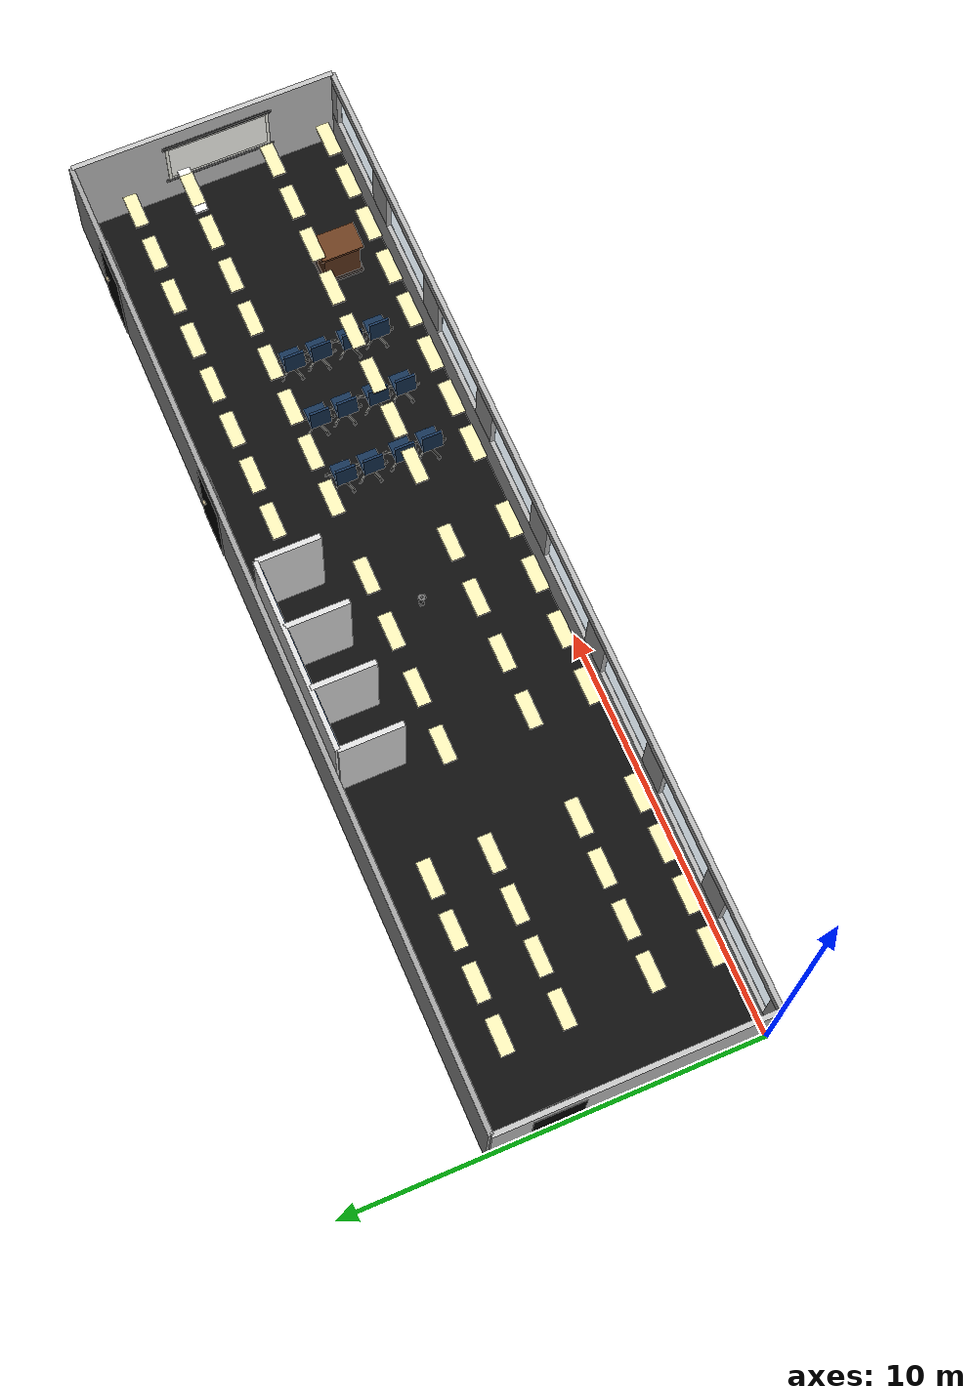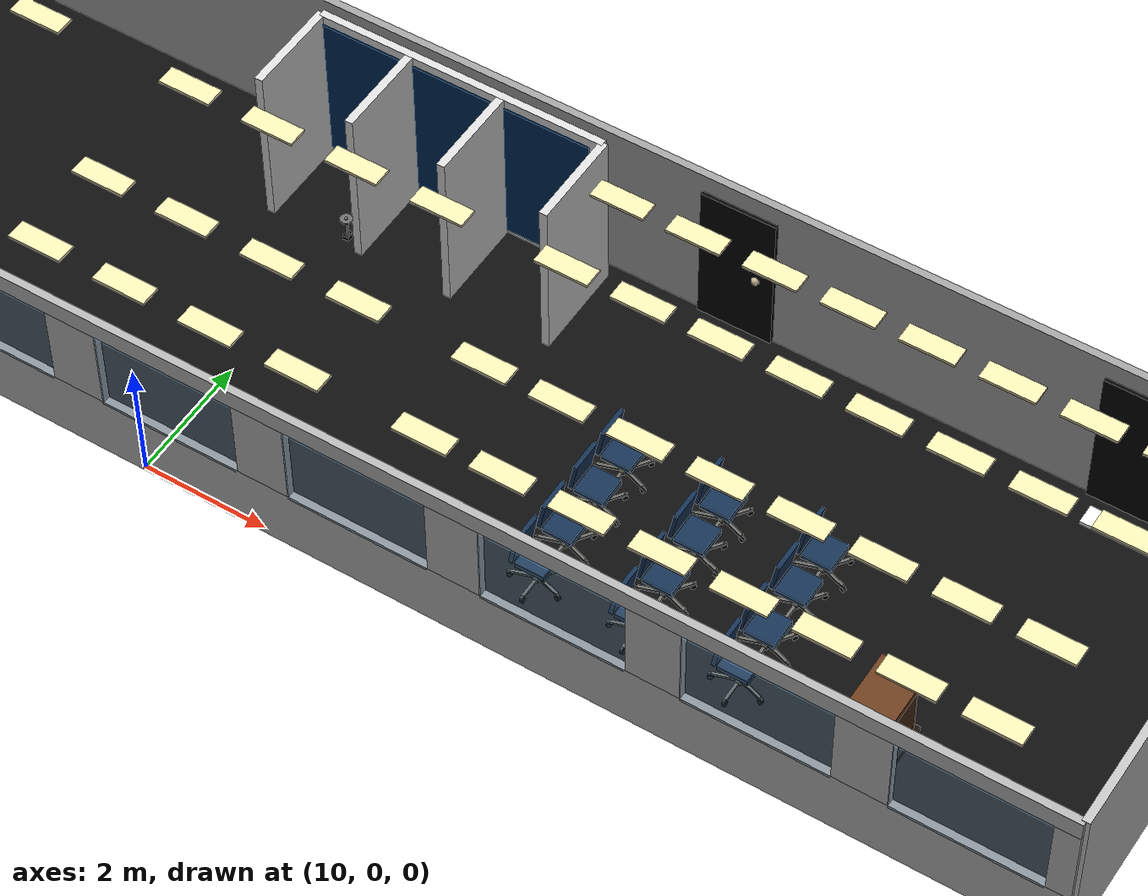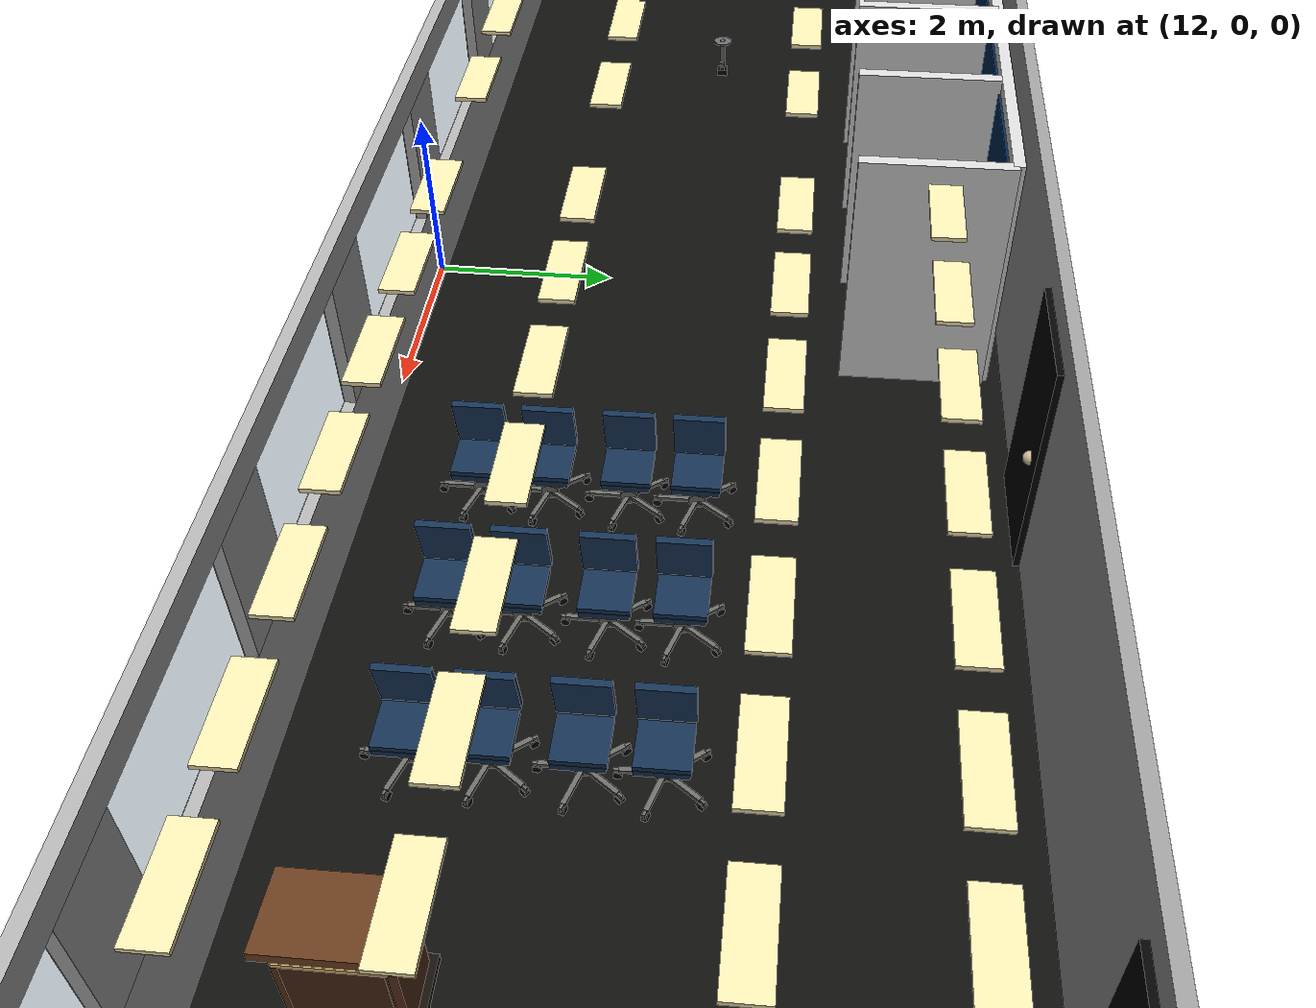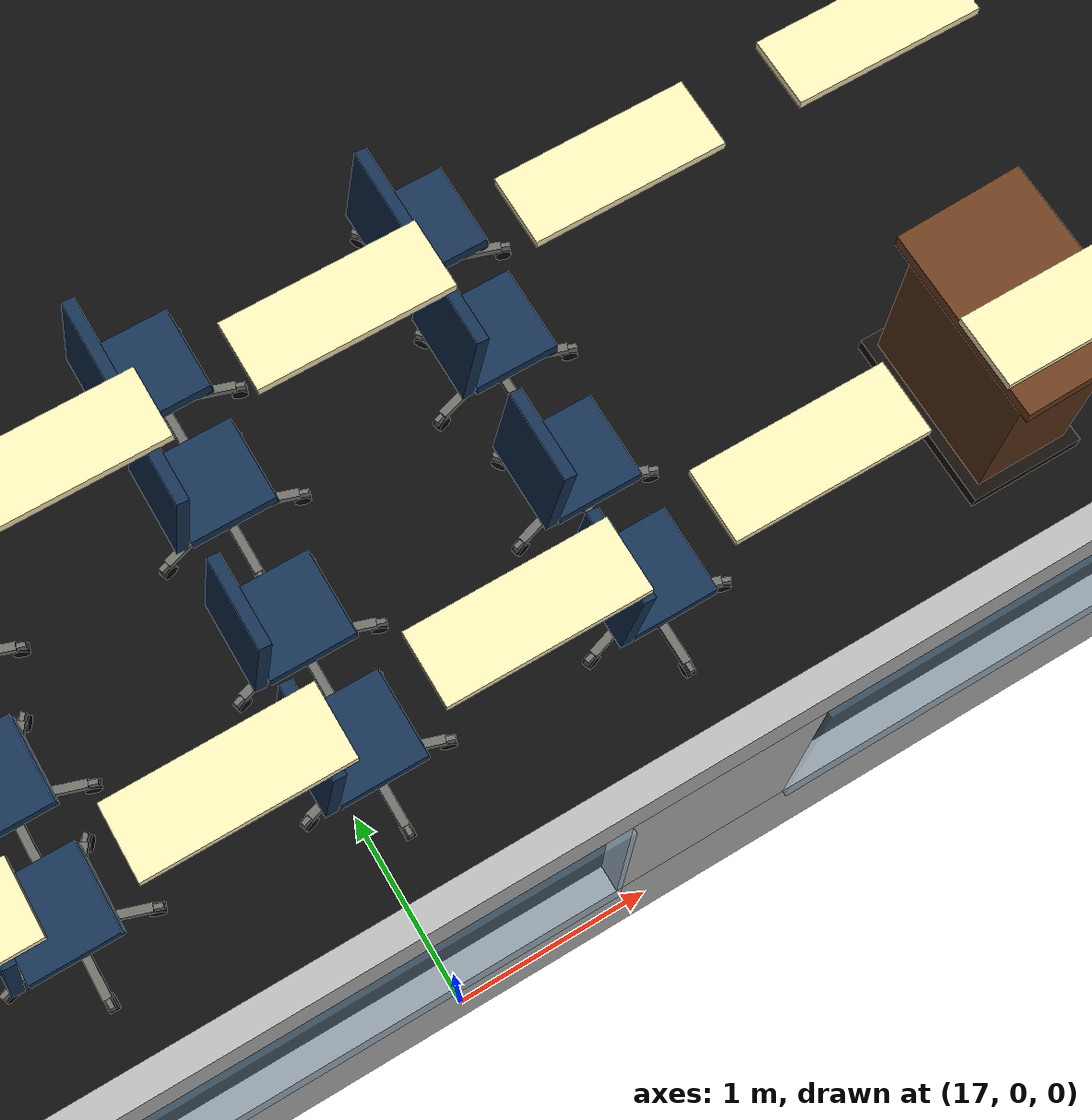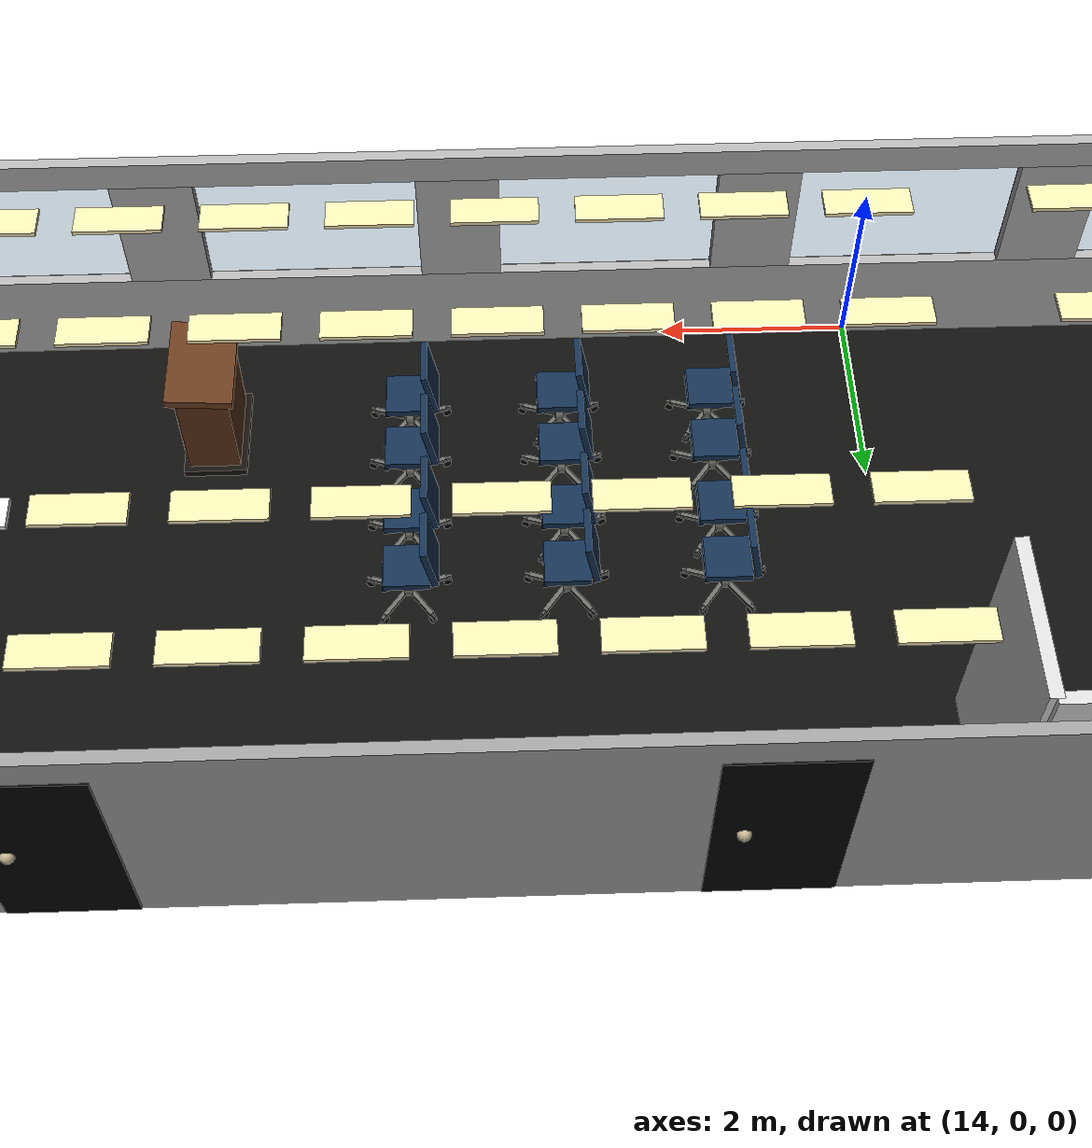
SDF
<sdf version="1.10">
 <world name="room_427">
  <plugin filename="gz-sim-physics-system" name="gz::sim::systems::Physics"/>
  <plugin filename="gz-sim-user-commands-system" name="gz::sim::systems::UserCommands"/>
  <plugin filename="gz-sim-scene-broadcaster-system" name="gz::sim::systems::SceneBroadcaster"/>
  <plugin filename="gz-sim-sensors-system" name="gz::sim::systems::Sensors">
   <render_engine>ogre2</render_engine>
  </plugin>
  <gravity>0 0 -9.8</gravity>
  <scene>
   <ambient>0.68 0.68 0.68 1</ambient>
   <background>0.82 0.86 0.9 1</background>
   <shadows>true</shadows>
   <grid>false</grid>
  </scene>
  <light name="main_light" type="directional">
   <pose>0 0 10 0 0 0</pose>
   <diffuse>1.0 1.0 0.95 1</diffuse>
   <specular>0.35 0.35 0.32 1</specular>
   <direction>-0.5 0.5 -1</direction>
  </light>
  <light name="room_427_fill_light_1" type="point">
   <pose>4.0 1.5 2.55 0 0 0</pose>
   <diffuse>0.85 0.82 0.72 1</diffuse>
   <specular>0.12 0.12 0.1 1</specular>
   <attenuation>
    <range>8.5</range>
    <constant>0.6</constant>
    <linear>0.08</linear>
    <quadratic>0.02</quadratic>
   </attenuation>
   <cast_shadows>false</cast_shadows>
  </light>
  <light name="room_427_fill_light_2" type="point">
   <pose>10.5 4.0 2.55 0 0 0</pose>
   <diffuse>0.85 0.82 0.72 1</diffuse>
   <specular>0.12 0.12 0.1 1</specular>
   <attenuation>
    <range>8.5</range>
    <constant>0.6</constant>
    <linear>0.08</linear>
    <quadratic>0.02</quadratic>
   </attenuation>
   <cast_shadows>false</cast_shadows>
  </light>
  <light name="room_427_fill_light_3" type="point">
   <pose>17.0 1.5 2.55 0 0 0</pose>
   <diffuse>0.85 0.82 0.72 1</diffuse>
   <specular>0.12 0.12 0.1 1</specular>
   <attenuation>
    <range>8.5</range>
    <constant>0.6</constant>
    <linear>0.08</linear>
    <quadratic>0.02</quadratic>
   </attenuation>
   <cast_shadows>false</cast_shadows>
  </light>
  <light name="room_427_fill_light_4" type="point">
   <pose>21.5 4.0 2.55 0 0 0</pose>
   <diffuse>0.85 0.82 0.72 1</diffuse>
   <specular>0.12 0.12 0.1 1</specular>
   <attenuation>
    <range>8.5</range>
    <constant>0.6</constant>
    <linear>0.08</linear>
    <quadratic>0.02</quadratic>
   </attenuation>
   <cast_shadows>false</cast_shadows>
  </light>
  <model name="room_427_floor">
   <static>true</static>
   <pose>12.1 3.27 0 0 0 0</pose>
   <link name="floor_link">
    <collision name="floor_collision"><geometry><box><size>24.2 6.54 0.03</size></box></geometry></collision>
    <visual name="floor_visual">
     <geometry><box><size>24.2 6.54 0.03</size></box></geometry>
     <material>
      <ambient>0.01 0.01 0.01 1</ambient>
      <diffuse>0.055 0.055 0.052 1</diffuse>
      <specular>0.45 0.45 0.42 1</specular>
      <pbr><metal><metalness>0.0</metalness><roughness>0.28</roughness></metal></pbr>
     </material>
    </visual>
   </link>
  </model>
  <model name="back_wall_D_C">
   <static>true</static>
   <pose>12.1 6.54 1.375 0 0 0</pose>
   <link name="link">
    <collision name="collision"><geometry><box><size>24.2 0.12 2.75</size></box></geometry></collision>
    <visual name="visual">
     <geometry><box><size>24.2 0.12 2.75</size></box></geometry>
     <material><ambient>0.62 0.62 0.62 1</ambient><diffuse>0.62 0.62 0.62 1</diffuse></material>
    </visual>
   </link>
  </model>
  <model name="wall_A_C_solid_no_door">
   <static>true</static>
   <pose>24.2 3.27 1.375 0 0 0</pose>
   <link name="link">
    <collision name="collision"><geometry><box><size>0.12 6.54 2.75</size></box></geometry></collision>
    <visual name="visual">
     <geometry><box><size>0.12 6.54 2.75</size></box></geometry>
     <material><ambient>0.75 0.75 0.75 1</ambient><diffuse>0.75 0.75 0.75 1</diffuse></material>
    </visual>
   </link>
  </model>
  <model name="B_D_wall_solid_with_door3_panel">
   <static>true</static>
   <pose>0 3.27 1.375 0 0 0</pose>
   <link name="wall_B_D_solid">
    <collision name="collision"><geometry><box><size>0.12 6.54 2.75</size></box></geometry></collision>
    <visual name="visual">
     <geometry><box><size>0.12 6.54 2.75</size></box></geometry>
     <material><ambient>0.75 0.75 0.75 1</ambient><diffuse>0.75 0.75 0.75 1</diffuse></material>
    </visual>
   </link>
   <link name="door_3_panel_near_D">
    <pose>0.065 1.5682 -0.16 0 0 0</pose>
    <visual name="visual">
     <geometry><box><size>0.04 0.9144 2.43</size></box></geometry>
     <material><ambient>0.45 0.45 0.45 1</ambient><diffuse>0.45 0.45 0.45 1</diffuse></material>
    </visual>
   </link>
  </model>
  <model name="window_wall_lower_A_B">
   <static>true</static>
   <pose>12.1 0 0.545 0 0 0</pose>
   <link name="link">
    <collision name="collision"><geometry><box><size>24.2 0.12 1.09</size></box></geometry></collision>
    <visual name="visual">
     <geometry><box><size>24.2 0.12 1.09</size></box></geometry>
     <material><ambient>0.7 0.7 0.7 1</ambient><diffuse>0.7 0.7 0.7 1</diffuse></material>
    </visual>
   </link>
  </model>
  <model name="window_wall_top_A_B">
   <static>true</static>
   <pose>12.1 0 2.5925 0 0 0</pose>
   <link name="link">
    <collision name="collision"><geometry><box><size>24.2 0.12 0.305</size></box></geometry></collision>
    <visual name="visual">
     <geometry><box><size>24.2 0.12 0.305</size></box></geometry>
     <material><ambient>0.7 0.7 0.7 1</ambient><diffuse>0.7 0.7 0.7 1</diffuse></material>
    </visual>
   </link>
  </model>
  <model name="window_wall_vertical_pieces">
   <static>true</static>
   <link name="window_side_left">
    <pose>0.1725 0 1.765 0 0 0</pose>
    <collision name="collision"><geometry><box><size>0.345 0.12 1.35</size></box></geometry></collision>
    <visual name="visual">
     <geometry><box><size>0.345 0.12 1.35</size></box></geometry>
     <material><ambient>0.7 0.7 0.7 1</ambient><diffuse>0.7 0.7 0.7 1</diffuse></material>
    </visual>
   </link>
   <link name="window_gap_1">
    <pose>2.97 0 1.765 0 0 0</pose>
    <collision name="collision"><geometry><box><size>0.83 0.12 1.35</size></box></geometry></collision>
    <visual name="visual">
     <geometry><box><size>0.83 0.12 1.35</size></box></geometry>
     <material><ambient>0.7 0.7 0.7 1</ambient><diffuse>0.7 0.7 0.7 1</diffuse></material>
    </visual>
   </link>
   <link name="window_gap_2">
    <pose>6.01 0 1.765 0 0 0</pose>
    <collision name="collision"><geometry><box><size>0.83 0.12 1.35</size></box></geometry></collision>
    <visual name="visual">
     <geometry><box><size>0.83 0.12 1.35</size></box></geometry>
     <material><ambient>0.7 0.7 0.7 1</ambient><diffuse>0.7 0.7 0.7 1</diffuse></material>
    </visual>
   </link>
   <link name="window_gap_3">
    <pose>9.05 0 1.765 0 0 0</pose>
    <collision name="collision"><geometry><box><size>0.83 0.12 1.35</size></box></geometry></collision>
    <visual name="visual">
     <geometry><box><size>0.83 0.12 1.35</size></box></geometry>
     <material><ambient>0.7 0.7 0.7 1</ambient><diffuse>0.7 0.7 0.7 1</diffuse></material>
    </visual>
   </link>
   <link name="window_gap_4">
    <pose>12.09 0 1.765 0 0 0</pose>
    <collision name="collision"><geometry><box><size>0.83 0.12 1.35</size></box></geometry></collision>
    <visual name="visual">
     <geometry><box><size>0.83 0.12 1.35</size></box></geometry>
     <material><ambient>0.7 0.7 0.7 1</ambient><diffuse>0.7 0.7 0.7 1</diffuse></material>
    </visual>
   </link>
   <link name="window_gap_5">
    <pose>15.13 0 1.765 0 0 0</pose>
    <collision name="collision"><geometry><box><size>0.83 0.12 1.35</size></box></geometry></collision>
    <visual name="visual">
     <geometry><box><size>0.83 0.12 1.35</size></box></geometry>
     <material><ambient>0.7 0.7 0.7 1</ambient><diffuse>0.7 0.7 0.7 1</diffuse></material>
    </visual>
   </link>
   <link name="window_gap_6">
    <pose>18.17 0 1.765 0 0 0</pose>
    <collision name="collision"><geometry><box><size>0.83 0.12 1.35</size></box></geometry></collision>
    <visual name="visual">
     <geometry><box><size>0.83 0.12 1.35</size></box></geometry>
     <material><ambient>0.7 0.7 0.7 1</ambient><diffuse>0.7 0.7 0.7 1</diffuse></material>
    </visual>
   </link>
   <link name="window_gap_7">
    <pose>21.21 0 1.765 0 0 0</pose>
    <collision name="collision"><geometry><box><size>0.83 0.12 1.35</size></box></geometry></collision>
    <visual name="visual">
     <geometry><box><size>0.83 0.12 1.35</size></box></geometry>
     <material><ambient>0.7 0.7 0.7 1</ambient><diffuse>0.7 0.7 0.7 1</diffuse></material>
    </visual>
   </link>
   <link name="window_side_right">
    <pose>24.0175 0 1.765 0 0 0</pose>
    <collision name="collision"><geometry><box><size>0.365 0.12 1.35</size></box></geometry></collision>
    <visual name="visual">
     <geometry><box><size>0.365 0.12 1.35</size></box></geometry>
     <material><ambient>0.7 0.7 0.7 1</ambient><diffuse>0.7 0.7 0.7 1</diffuse></material>
    </visual>
   </link>
  </model>
  <model name="window_glass_panes">
   <static>true</static>
   <link name="window_1">
    <pose>1.45 -0.07 1.765 0 0 0</pose>
    <visual name="visual">
     <geometry><box><size>2.21 0.03 1.35</size></box></geometry>
     <material>
      <ambient>0.55 0.75 0.9 0.35</ambient>
      <diffuse>0.55 0.75 0.9 0.35</diffuse>
      <specular>0.8 0.8 0.8 1</specular>
     </material>
     <transparency>0.55</transparency>
    </visual>
   </link>
   <link name="window_2">
    <pose>4.49 -0.07 1.765 0 0 0</pose>
    <visual name="visual">
     <geometry><box><size>2.21 0.03 1.35</size></box></geometry>
     <material>
      <ambient>0.55 0.75 0.9 0.35</ambient>
      <diffuse>0.55 0.75 0.9 0.35</diffuse>
      <specular>0.8 0.8 0.8 1</specular>
     </material>
     <transparency>0.55</transparency>
    </visual>
   </link>
   <link name="window_3">
    <pose>7.53 -0.07 1.765 0 0 0</pose>
    <visual name="visual">
     <geometry><box><size>2.21 0.03 1.35</size></box></geometry>
     <material>
      <ambient>0.55 0.75 0.9 0.35</ambient>
      <diffuse>0.55 0.75 0.9 0.35</diffuse>
      <specular>0.8 0.8 0.8 1</specular>
     </material>
     <transparency>0.55</transparency>
    </visual>
   </link>
   <link name="window_4">
    <pose>10.57 -0.07 1.765 0 0 0</pose>
    <visual name="visual">
     <geometry><box><size>2.21 0.03 1.35</size></box></geometry>
     <material>
      <ambient>0.55 0.75 0.9 0.35</ambient>
      <diffuse>0.55 0.75 0.9 0.35</diffuse>
      <specular>0.8 0.8 0.8 1</specular>
     </material>
     <transparency>0.55</transparency>
    </visual>
   </link>
   <link name="window_5">
    <pose>13.61 -0.07 1.765 0 0 0</pose>
    <visual name="visual">
     <geometry><box><size>2.21 0.03 1.35</size></box></geometry>
     <material>
      <ambient>0.55 0.75 0.9 0.35</ambient>
      <diffuse>0.55 0.75 0.9 0.35</diffuse>
      <specular>0.8 0.8 0.8 1</specular>
     </material>
     <transparency>0.55</transparency>
    </visual>
   </link>
   <link name="window_6">
    <pose>16.65 -0.07 1.765 0 0 0</pose>
    <visual name="visual">
     <geometry><box><size>2.21 0.03 1.35</size></box></geometry>
     <material>
      <ambient>0.55 0.75 0.9 0.35</ambient>
      <diffuse>0.55 0.75 0.9 0.35</diffuse>
      <specular>0.8 0.8 0.8 1</specular>
     </material>
     <transparency>0.55</transparency>
    </visual>
   </link>
   <link name="window_7">
    <pose>19.69 -0.07 1.765 0 0 0</pose>
    <visual name="visual">
     <geometry><box><size>2.21 0.03 1.35</size></box></geometry>
     <material>
      <ambient>0.55 0.75 0.9 0.35</ambient>
      <diffuse>0.55 0.75 0.9 0.35</diffuse>
      <specular>0.8 0.8 0.8 1</specular>
     </material>
     <transparency>0.55</transparency>
    </visual>
   </link>
   <link name="window_8">
    <pose>22.73 -0.07 1.765 0 0 0</pose>
    <visual name="visual">
     <geometry><box><size>2.21 0.03 1.35</size></box></geometry>
     <material>
      <ambient>0.55 0.75 0.9 0.35</ambient>
      <diffuse>0.55 0.75 0.9 0.35</diffuse>
      <specular>0.8 0.8 0.8 1</specular>
     </material>
     <transparency>0.55</transparency>
    </visual>
   </link>
  </model>
  <model name="ceiling_lights_zone1">
   <static>true</static>
   <link name="ceiling_lights_zone1_r1_c1">
    <pose>1.8 0.75 2.70 0 0 0</pose>
    <visual name="visual">
     <geometry><box><size>0.85 0.32 0.04</size></box></geometry>
     <material>
      <ambient>1.0 0.92 0.7 1</ambient>
      <diffuse>1.0 0.92 0.7 1</diffuse>
      <emissive>1.0 0.92 0.7 1</emissive>
     </material>
    </visual>
   </link>
   <link name="ceiling_lights_zone1_r1_c2">
    <pose>1.8 2.15 2.70 0 0 0</pose>
    <visual name="visual">
     <geometry><box><size>0.85 0.32 0.04</size></box></geometry>
     <material>
      <ambient>1.0 0.92 0.7 1</ambient>
      <diffuse>1.0 0.92 0.7 1</diffuse>
      <emissive>1.0 0.92 0.7 1</emissive>
     </material>
    </visual>
   </link>
   <link name="ceiling_lights_zone1_r1_c3">
    <pose>1.8 4.15 2.70 0 0 0</pose>
    <visual name="visual">
     <geometry><box><size>0.85 0.32 0.04</size></box></geometry>
     <material>
      <ambient>1.0 0.92 0.7 1</ambient>
      <diffuse>1.0 0.92 0.7 1</diffuse>
      <emissive>1.0 0.92 0.7 1</emissive>
     </material>
    </visual>
   </link>
   <link name="ceiling_lights_zone1_r1_c4">
    <pose>1.8 5.55 2.70 0 0 0</pose>
    <visual name="visual">
     <geometry><box><size>0.85 0.32 0.04</size></box></geometry>
     <material>
      <ambient>1.0 0.92 0.7 1</ambient>
      <diffuse>1.0 0.92 0.7 1</diffuse>
      <emissive>1.0 0.92 0.7 1</emissive>
     </material>
    </visual>
   </link>
   <link name="ceiling_lights_zone1_r2_c1">
    <pose>3.0 0.75 2.70 0 0 0</pose>
    <visual name="visual">
     <geometry><box><size>0.85 0.32 0.04</size></box></geometry>
     <material>
      <ambient>1.0 0.92 0.7 1</ambient>
      <diffuse>1.0 0.92 0.7 1</diffuse>
      <emissive>1.0 0.92 0.7 1</emissive>
     </material>
    </visual>
   </link>
   <link name="ceiling_lights_zone1_r2_c2">
    <pose>3.0 2.15 2.70 0 0 0</pose>
    <visual name="visual">
     <geometry><box><size>0.85 0.32 0.04</size></box></geometry>
     <material>
      <ambient>1.0 0.92 0.7 1</ambient>
      <diffuse>1.0 0.92 0.7 1</diffuse>
      <emissive>1.0 0.92 0.7 1</emissive>
     </material>
    </visual>
   </link>
   <link name="ceiling_lights_zone1_r2_c3">
    <pose>3.0 4.15 2.70 0 0 0</pose>
    <visual name="visual">
     <geometry><box><size>0.85 0.32 0.04</size></box></geometry>
     <material>
      <ambient>1.0 0.92 0.7 1</ambient>
      <diffuse>1.0 0.92 0.7 1</diffuse>
      <emissive>1.0 0.92 0.7 1</emissive>
     </material>
    </visual>
   </link>
   <link name="ceiling_lights_zone1_r2_c4">
    <pose>3.0 5.55 2.70 0 0 0</pose>
    <visual name="visual">
     <geometry><box><size>0.85 0.32 0.04</size></box></geometry>
     <material>
      <ambient>1.0 0.92 0.7 1</ambient>
      <diffuse>1.0 0.92 0.7 1</diffuse>
      <emissive>1.0 0.92 0.7 1</emissive>
     </material>
    </visual>
   </link>
   <link name="ceiling_lights_zone1_r3_c1">
    <pose>4.2 0.75 2.70 0 0 0</pose>
    <visual name="visual">
     <geometry><box><size>0.85 0.32 0.04</size></box></geometry>
     <material>
      <ambient>1.0 0.92 0.7 1</ambient>
      <diffuse>1.0 0.92 0.7 1</diffuse>
      <emissive>1.0 0.92 0.7 1</emissive>
     </material>
    </visual>
   </link>
   <link name="ceiling_lights_zone1_r3_c2">
    <pose>4.2 2.15 2.70 0 0 0</pose>
    <visual name="visual">
     <geometry><box><size>0.85 0.32 0.04</size></box></geometry>
     <material>
      <ambient>1.0 0.92 0.7 1</ambient>
      <diffuse>1.0 0.92 0.7 1</diffuse>
      <emissive>1.0 0.92 0.7 1</emissive>
     </material>
    </visual>
   </link>
   <link name="ceiling_lights_zone1_r3_c3">
    <pose>4.2 4.15 2.70 0 0 0</pose>
    <visual name="visual">
     <geometry><box><size>0.85 0.32 0.04</size></box></geometry>
     <material>
      <ambient>1.0 0.92 0.7 1</ambient>
      <diffuse>1.0 0.92 0.7 1</diffuse>
      <emissive>1.0 0.92 0.7 1</emissive>
     </material>
    </visual>
   </link>
   <link name="ceiling_lights_zone1_r3_c4">
    <pose>4.2 5.55 2.70 0 0 0</pose>
    <visual name="visual">
     <geometry><box><size>0.85 0.32 0.04</size></box></geometry>
     <material>
      <ambient>1.0 0.92 0.7 1</ambient>
      <diffuse>1.0 0.92 0.7 1</diffuse>
      <emissive>1.0 0.92 0.7 1</emissive>
     </material>
    </visual>
   </link>
   <link name="ceiling_lights_zone1_r4_c1">
    <pose>5.4 0.75 2.70 0 0 0</pose>
    <visual name="visual">
     <geometry><box><size>0.85 0.32 0.04</size></box></geometry>
     <material>
      <ambient>1.0 0.92 0.7 1</ambient>
      <diffuse>1.0 0.92 0.7 1</diffuse>
      <emissive>1.0 0.92 0.7 1</emissive>
     </material>
    </visual>
   </link>
   <link name="ceiling_lights_zone1_r4_c2">
    <pose>5.4 2.15 2.70 0 0 0</pose>
    <visual name="visual">
     <geometry><box><size>0.85 0.32 0.04</size></box></geometry>
     <material>
      <ambient>1.0 0.92 0.7 1</ambient>
      <diffuse>1.0 0.92 0.7 1</diffuse>
      <emissive>1.0 0.92 0.7 1</emissive>
     </material>
    </visual>
   </link>
   <link name="ceiling_lights_zone1_r4_c3">
    <pose>5.4 4.15 2.70 0 0 0</pose>
    <visual name="visual">
     <geometry><box><size>0.85 0.32 0.04</size></box></geometry>
     <material>
      <ambient>1.0 0.92 0.7 1</ambient>
      <diffuse>1.0 0.92 0.7 1</diffuse>
      <emissive>1.0 0.92 0.7 1</emissive>
     </material>
    </visual>
   </link>
   <link name="ceiling_lights_zone1_r4_c4">
    <pose>5.4 5.55 2.70 0 0 0</pose>
    <visual name="visual">
     <geometry><box><size>0.85 0.32 0.04</size></box></geometry>
     <material>
      <ambient>1.0 0.92 0.7 1</ambient>
      <diffuse>1.0 0.92 0.7 1</diffuse>
      <emissive>1.0 0.92 0.7 1</emissive>
     </material>
    </visual>
   </link>
  </model>
  <model name="ceiling_lights_zone2">
   <static>true</static>
   <link name="ceiling_lights_zone2_r1_c1">
    <pose>8.0 0.75 2.70 0 0 0</pose>
    <visual name="visual">
     <geometry><box><size>0.85 0.32 0.04</size></box></geometry>
     <material>
      <ambient>1.0 0.92 0.7 1</ambient>
      <diffuse>1.0 0.92 0.7 1</diffuse>
      <emissive>1.0 0.92 0.7 1</emissive>
     </material>
    </visual>
   </link>
   <link name="ceiling_lights_zone2_r1_c2">
    <pose>8.0 2.15 2.70 0 0 0</pose>
    <visual name="visual">
     <geometry><box><size>0.85 0.32 0.04</size></box></geometry>
     <material>
      <ambient>1.0 0.92 0.7 1</ambient>
      <diffuse>1.0 0.92 0.7 1</diffuse>
      <emissive>1.0 0.92 0.7 1</emissive>
     </material>
    </visual>
   </link>
   <link name="ceiling_lights_zone2_r1_c3">
    <pose>8.0 4.15 2.70 0 0 0</pose>
    <visual name="visual">
     <geometry><box><size>0.85 0.32 0.04</size></box></geometry>
     <material>
      <ambient>1.0 0.92 0.7 1</ambient>
      <diffuse>1.0 0.92 0.7 1</diffuse>
      <emissive>1.0 0.92 0.7 1</emissive>
     </material>
    </visual>
   </link>
   <link name="ceiling_lights_zone2_r2_c1">
    <pose>9.4 0.75 2.70 0 0 0</pose>
    <visual name="visual">
     <geometry><box><size>0.85 0.32 0.04</size></box></geometry>
     <material>
      <ambient>1.0 0.92 0.7 1</ambient>
      <diffuse>1.0 0.92 0.7 1</diffuse>
      <emissive>1.0 0.92 0.7 1</emissive>
     </material>
    </visual>
   </link>
   <link name="ceiling_lights_zone2_r2_c2">
    <pose>9.4 2.15 2.70 0 0 0</pose>
    <visual name="visual">
     <geometry><box><size>0.85 0.32 0.04</size></box></geometry>
     <material>
      <ambient>1.0 0.92 0.7 1</ambient>
      <diffuse>1.0 0.92 0.7 1</diffuse>
      <emissive>1.0 0.92 0.7 1</emissive>
     </material>
    </visual>
   </link>
   <link name="ceiling_lights_zone2_r2_c3">
    <pose>9.4 4.15 2.70 0 0 0</pose>
    <visual name="visual">
     <geometry><box><size>0.85 0.32 0.04</size></box></geometry>
     <material>
      <ambient>1.0 0.92 0.7 1</ambient>
      <diffuse>1.0 0.92 0.7 1</diffuse>
      <emissive>1.0 0.92 0.7 1</emissive>
     </material>
    </visual>
   </link>
   <link name="ceiling_lights_zone2_r3_c1">
    <pose>10.8 0.75 2.70 0 0 0</pose>
    <visual name="visual">
     <geometry><box><size>0.85 0.32 0.04</size></box></geometry>
     <material>
      <ambient>1.0 0.92 0.7 1</ambient>
      <diffuse>1.0 0.92 0.7 1</diffuse>
      <emissive>1.0 0.92 0.7 1</emissive>
     </material>
    </visual>
   </link>
   <link name="ceiling_lights_zone2_r3_c2">
    <pose>10.8 2.15 2.70 0 0 0</pose>
    <visual name="visual">
     <geometry><box><size>0.85 0.32 0.04</size></box></geometry>
     <material>
      <ambient>1.0 0.92 0.7 1</ambient>
      <diffuse>1.0 0.92 0.7 1</diffuse>
      <emissive>1.0 0.92 0.7 1</emissive>
     </material>
    </visual>
   </link>
   <link name="ceiling_lights_zone2_r3_c3">
    <pose>10.8 4.15 2.70 0 0 0</pose>
    <visual name="visual">
     <geometry><box><size>0.85 0.32 0.04</size></box></geometry>
     <material>
      <ambient>1.0 0.92 0.7 1</ambient>
      <diffuse>1.0 0.92 0.7 1</diffuse>
      <emissive>1.0 0.92 0.7 1</emissive>
     </material>
    </visual>
   </link>
   <link name="ceiling_lights_zone2_r4_c1">
    <pose>12.2 0.75 2.70 0 0 0</pose>
    <visual name="visual">
     <geometry><box><size>0.85 0.32 0.04</size></box></geometry>
     <material>
      <ambient>1.0 0.92 0.7 1</ambient>
      <diffuse>1.0 0.92 0.7 1</diffuse>
      <emissive>1.0 0.92 0.7 1</emissive>
     </material>
    </visual>
   </link>
   <link name="ceiling_lights_zone2_r4_c2">
    <pose>12.2 2.15 2.70 0 0 0</pose>
    <visual name="visual">
     <geometry><box><size>0.85 0.32 0.04</size></box></geometry>
     <material>
      <ambient>1.0 0.92 0.7 1</ambient>
      <diffuse>1.0 0.92 0.7 1</diffuse>
      <emissive>1.0 0.92 0.7 1</emissive>
     </material>
    </visual>
   </link>
   <link name="ceiling_lights_zone2_r4_c3">
    <pose>12.2 4.15 2.70 0 0 0</pose>
    <visual name="visual">
     <geometry><box><size>0.85 0.32 0.04</size></box></geometry>
     <material>
      <ambient>1.0 0.92 0.7 1</ambient>
      <diffuse>1.0 0.92 0.7 1</diffuse>
      <emissive>1.0 0.92 0.7 1</emissive>
     </material>
    </visual>
   </link>
  </model>
  <model name="ceiling_lights_zone3">
   <static>true</static>
   <link name="ceiling_lights_zone3_r1_c1">
    <pose>14.2 0.75 2.70 0 0 0</pose>
    <visual name="visual">
     <geometry><box><size>0.85 0.32 0.04</size></box></geometry>
     <material>
      <ambient>1.0 0.92 0.7 1</ambient>
      <diffuse>1.0 0.92 0.7 1</diffuse>
      <emissive>1.0 0.92 0.7 1</emissive>
     </material>
    </visual>
   </link>
   <link name="ceiling_lights_zone3_r1_c2">
    <pose>14.2 2.15 2.70 0 0 0</pose>
    <visual name="visual">
     <geometry><box><size>0.85 0.32 0.04</size></box></geometry>
     <material>
      <ambient>1.0 0.92 0.7 1</ambient>
      <diffuse>1.0 0.92 0.7 1</diffuse>
      <emissive>1.0 0.92 0.7 1</emissive>
     </material>
    </visual>
   </link>
   <link name="ceiling_lights_zone3_r1_c3">
    <pose>14.2 4.15 2.70 0 0 0</pose>
    <visual name="visual">
     <geometry><box><size>0.85 0.32 0.04</size></box></geometry>
     <material>
      <ambient>1.0 0.92 0.7 1</ambient>
      <diffuse>1.0 0.92 0.7 1</diffuse>
      <emissive>1.0 0.92 0.7 1</emissive>
     </material>
    </visual>
   </link>
   <link name="ceiling_lights_zone3_r1_c4">
    <pose>14.2 5.55 2.70 0 0 0</pose>
    <visual name="visual">
     <geometry><box><size>0.85 0.32 0.04</size></box></geometry>
     <material>
      <ambient>1.0 0.92 0.7 1</ambient>
      <diffuse>1.0 0.92 0.7 1</diffuse>
      <emissive>1.0 0.92 0.7 1</emissive>
     </material>
    </visual>
   </link>
   <link name="ceiling_lights_zone3_r2_c1">
    <pose>15.4 0.75 2.70 0 0 0</pose>
    <visual name="visual">
     <geometry><box><size>0.85 0.32 0.04</size></box></geometry>
     <material>
      <ambient>1.0 0.92 0.7 1</ambient>
      <diffuse>1.0 0.92 0.7 1</diffuse>
      <emissive>1.0 0.92 0.7 1</emissive>
     </material>
    </visual>
   </link>
   <link name="ceiling_lights_zone3_r2_c2">
    <pose>15.4 2.15 2.70 0 0 0</pose>
    <visual name="visual">
     <geometry><box><size>0.85 0.32 0.04</size></box></geometry>
     <material>
      <ambient>1.0 0.92 0.7 1</ambient>
      <diffuse>1.0 0.92 0.7 1</diffuse>
      <emissive>1.0 0.92 0.7 1</emissive>
     </material>
    </visual>
   </link>
   <link name="ceiling_lights_zone3_r2_c3">
    <pose>15.4 4.15 2.70 0 0 0</pose>
    <visual name="visual">
     <geometry><box><size>0.85 0.32 0.04</size></box></geometry>
     <material>
      <ambient>1.0 0.92 0.7 1</ambient>
      <diffuse>1.0 0.92 0.7 1</diffuse>
      <emissive>1.0 0.92 0.7 1</emissive>
     </material>
    </visual>
   </link>
   <link name="ceiling_lights_zone3_r2_c4">
    <pose>15.4 5.55 2.70 0 0 0</pose>
    <visual name="visual">
     <geometry><box><size>0.85 0.32 0.04</size></box></geometry>
     <material>
      <ambient>1.0 0.92 0.7 1</ambient>
      <diffuse>1.0 0.92 0.7 1</diffuse>
      <emissive>1.0 0.92 0.7 1</emissive>
     </material>
    </visual>
   </link>
   <link name="ceiling_lights_zone3_r3_c1">
    <pose>16.6 0.75 2.70 0 0 0</pose>
    <visual name="visual">
     <geometry><box><size>0.85 0.32 0.04</size></box></geometry>
     <material>
      <ambient>1.0 0.92 0.7 1</ambient>
      <diffuse>1.0 0.92 0.7 1</diffuse>
      <emissive>1.0 0.92 0.7 1</emissive>
     </material>
    </visual>
   </link>
   <link name="ceiling_lights_zone3_r3_c2">
    <pose>16.6 2.15 2.70 0 0 0</pose>
    <visual name="visual">
     <geometry><box><size>0.85 0.32 0.04</size></box></geometry>
     <material>
      <ambient>1.0 0.92 0.7 1</ambient>
      <diffuse>1.0 0.92 0.7 1</diffuse>
      <emissive>1.0 0.92 0.7 1</emissive>
     </material>
    </visual>
   </link>
   <link name="ceiling_lights_zone3_r3_c3">
    <pose>16.6 4.15 2.70 0 0 0</pose>
    <visual name="visual">
     <geometry><box><size>0.85 0.32 0.04</size></box></geometry>
     <material>
      <ambient>1.0 0.92 0.7 1</ambient>
      <diffuse>1.0 0.92 0.7 1</diffuse>
      <emissive>1.0 0.92 0.7 1</emissive>
     </material>
    </visual>
   </link>
   <link name="ceiling_lights_zone3_r3_c4">
    <pose>16.6 5.55 2.70 0 0 0</pose>
    <visual name="visual">
     <geometry><box><size>0.85 0.32 0.04</size></box></geometry>
     <material>
      <ambient>1.0 0.92 0.7 1</ambient>
      <diffuse>1.0 0.92 0.7 1</diffuse>
      <emissive>1.0 0.92 0.7 1</emissive>
     </material>
    </visual>
   </link>
   <link name="ceiling_lights_zone3_r4_c1">
    <pose>17.8 0.75 2.70 0 0 0</pose>
    <visual name="visual">
     <geometry><box><size>0.85 0.32 0.04</size></box></geometry>
     <material>
      <ambient>1.0 0.92 0.7 1</ambient>
      <diffuse>1.0 0.92 0.7 1</diffuse>
      <emissive>1.0 0.92 0.7 1</emissive>
     </material>
    </visual>
   </link>
   <link name="ceiling_lights_zone3_r4_c2">
    <pose>17.8 2.15 2.70 0 0 0</pose>
    <visual name="visual">
     <geometry><box><size>0.85 0.32 0.04</size></box></geometry>
     <material>
      <ambient>1.0 0.92 0.7 1</ambient>
      <diffuse>1.0 0.92 0.7 1</diffuse>
      <emissive>1.0 0.92 0.7 1</emissive>
     </material>
    </visual>
   </link>
   <link name="ceiling_lights_zone3_r4_c3">
    <pose>17.8 4.15 2.70 0 0 0</pose>
    <visual name="visual">
     <geometry><box><size>0.85 0.32 0.04</size></box></geometry>
     <material>
      <ambient>1.0 0.92 0.7 1</ambient>
      <diffuse>1.0 0.92 0.7 1</diffuse>
      <emissive>1.0 0.92 0.7 1</emissive>
     </material>
    </visual>
   </link>
   <link name="ceiling_lights_zone3_r4_c4">
    <pose>17.8 5.55 2.70 0 0 0</pose>
    <visual name="visual">
     <geometry><box><size>0.85 0.32 0.04</size></box></geometry>
     <material>
      <ambient>1.0 0.92 0.7 1</ambient>
      <diffuse>1.0 0.92 0.7 1</diffuse>
      <emissive>1.0 0.92 0.7 1</emissive>
     </material>
    </visual>
   </link>
   <link name="ceiling_lights_zone3_r5_c1">
    <pose>19.0 0.75 2.70 0 0 0</pose>
    <visual name="visual">
     <geometry><box><size>0.85 0.32 0.04</size></box></geometry>
     <material>
      <ambient>1.0 0.92 0.7 1</ambient>
      <diffuse>1.0 0.92 0.7 1</diffuse>
      <emissive>1.0 0.92 0.7 1</emissive>
     </material>
    </visual>
   </link>
   <link name="ceiling_lights_zone3_r5_c2">
    <pose>19.0 2.15 2.70 0 0 0</pose>
    <visual name="visual">
     <geometry><box><size>0.85 0.32 0.04</size></box></geometry>
     <material>
      <ambient>1.0 0.92 0.7 1</ambient>
      <diffuse>1.0 0.92 0.7 1</diffuse>
      <emissive>1.0 0.92 0.7 1</emissive>
     </material>
    </visual>
   </link>
   <link name="ceiling_lights_zone3_r5_c3">
    <pose>19.0 4.15 2.70 0 0 0</pose>
    <visual name="visual">
     <geometry><box><size>0.85 0.32 0.04</size></box></geometry>
     <material>
      <ambient>1.0 0.92 0.7 1</ambient>
      <diffuse>1.0 0.92 0.7 1</diffuse>
      <emissive>1.0 0.92 0.7 1</emissive>
     </material>
    </visual>
   </link>
   <link name="ceiling_lights_zone3_r5_c4">
    <pose>19.0 5.55 2.70 0 0 0</pose>
    <visual name="visual">
     <geometry><box><size>0.85 0.32 0.04</size></box></geometry>
     <material>
      <ambient>1.0 0.92 0.7 1</ambient>
      <diffuse>1.0 0.92 0.7 1</diffuse>
      <emissive>1.0 0.92 0.7 1</emissive>
     </material>
    </visual>
   </link>
   <link name="ceiling_lights_zone3_r6_c1">
    <pose>20.2 0.75 2.70 0 0 0</pose>
    <visual name="visual">
     <geometry><box><size>0.85 0.32 0.04</size></box></geometry>
     <material>
      <ambient>1.0 0.92 0.7 1</ambient>
      <diffuse>1.0 0.92 0.7 1</diffuse>
      <emissive>1.0 0.92 0.7 1</emissive>
     </material>
    </visual>
   </link>
   <link name="ceiling_lights_zone3_r6_c2">
    <pose>20.2 2.15 2.70 0 0 0</pose>
    <visual name="visual">
     <geometry><box><size>0.85 0.32 0.04</size></box></geometry>
     <material>
      <ambient>1.0 0.92 0.7 1</ambient>
      <diffuse>1.0 0.92 0.7 1</diffuse>
      <emissive>1.0 0.92 0.7 1</emissive>
     </material>
    </visual>
   </link>
   <link name="ceiling_lights_zone3_r6_c3">
    <pose>20.2 4.15 2.70 0 0 0</pose>
    <visual name="visual">
     <geometry><box><size>0.85 0.32 0.04</size></box></geometry>
     <material>
      <ambient>1.0 0.92 0.7 1</ambient>
      <diffuse>1.0 0.92 0.7 1</diffuse>
      <emissive>1.0 0.92 0.7 1</emissive>
     </material>
    </visual>
   </link>
   <link name="ceiling_lights_zone3_r6_c4">
    <pose>20.2 5.55 2.70 0 0 0</pose>
    <visual name="visual">
     <geometry><box><size>0.85 0.32 0.04</size></box></geometry>
     <material>
      <ambient>1.0 0.92 0.7 1</ambient>
      <diffuse>1.0 0.92 0.7 1</diffuse>
      <emissive>1.0 0.92 0.7 1</emissive>
     </material>
    </visual>
   </link>
   <link name="ceiling_lights_zone3_r7_c1">
    <pose>21.4 0.75 2.70 0 0 0</pose>
    <visual name="visual">
     <geometry><box><size>0.85 0.32 0.04</size></box></geometry>
     <material>
      <ambient>1.0 0.92 0.7 1</ambient>
      <diffuse>1.0 0.92 0.7 1</diffuse>
      <emissive>1.0 0.92 0.7 1</emissive>
     </material>
    </visual>
   </link>
   <link name="ceiling_lights_zone3_r7_c2">
    <pose>21.4 2.15 2.70 0 0 0</pose>
    <visual name="visual">
     <geometry><box><size>0.85 0.32 0.04</size></box></geometry>
     <material>
      <ambient>1.0 0.92 0.7 1</ambient>
      <diffuse>1.0 0.92 0.7 1</diffuse>
      <emissive>1.0 0.92 0.7 1</emissive>
     </material>
    </visual>
   </link>
   <link name="ceiling_lights_zone3_r7_c3">
    <pose>21.4 4.15 2.70 0 0 0</pose>
    <visual name="visual">
     <geometry><box><size>0.85 0.32 0.04</size></box></geometry>
     <material>
      <ambient>1.0 0.92 0.7 1</ambient>
      <diffuse>1.0 0.92 0.7 1</diffuse>
      <emissive>1.0 0.92 0.7 1</emissive>
     </material>
    </visual>
   </link>
   <link name="ceiling_lights_zone3_r7_c4">
    <pose>21.4 5.55 2.70 0 0 0</pose>
    <visual name="visual">
     <geometry><box><size>0.85 0.32 0.04</size></box></geometry>
     <material>
      <ambient>1.0 0.92 0.7 1</ambient>
      <diffuse>1.0 0.92 0.7 1</diffuse>
      <emissive>1.0 0.92 0.7 1</emissive>
     </material>
    </visual>
   </link>
   <link name="ceiling_lights_zone3_r8_c1">
    <pose>22.6 0.75 2.70 0 0 0</pose>
    <visual name="visual">
     <geometry><box><size>0.85 0.32 0.04</size></box></geometry>
     <material>
      <ambient>1.0 0.92 0.7 1</ambient>
      <diffuse>1.0 0.92 0.7 1</diffuse>
      <emissive>1.0 0.92 0.7 1</emissive>
     </material>
    </visual>
   </link>
   <link name="ceiling_lights_zone3_r8_c2">
    <pose>22.6 2.15 2.70 0 0 0</pose>
    <visual name="visual">
     <geometry><box><size>0.85 0.32 0.04</size></box></geometry>
     <material>
      <ambient>1.0 0.92 0.7 1</ambient>
      <diffuse>1.0 0.92 0.7 1</diffuse>
      <emissive>1.0 0.92 0.7 1</emissive>
     </material>
    </visual>
   </link>
   <link name="ceiling_lights_zone3_r8_c3">
    <pose>22.6 4.15 2.70 0 0 0</pose>
    <visual name="visual">
     <geometry><box><size>0.85 0.32 0.04</size></box></geometry>
     <material>
      <ambient>1.0 0.92 0.7 1</ambient>
      <diffuse>1.0 0.92 0.7 1</diffuse>
      <emissive>1.0 0.92 0.7 1</emissive>
     </material>
    </visual>
   </link>
   <link name="ceiling_lights_zone3_r8_c4">
    <pose>22.6 5.55 2.70 0 0 0</pose>
    <visual name="visual">
     <geometry><box><size>0.85 0.32 0.04</size></box></geometry>
     <material>
      <ambient>1.0 0.92 0.7 1</ambient>
      <diffuse>1.0 0.92 0.7 1</diffuse>
      <emissive>1.0 0.92 0.7 1</emissive>
     </material>
    </visual>
   </link>
  </model>
  <model name="doors_and_connected_boxes_on_D_C_wall">
   <static>true</static>
   <link name="boxes_back_wall">
    <pose>11.1 6.27 1.375 0 0 0</pose>
    <collision name="collision"><geometry><box><size>4.699 0.12 2.75</size></box></geometry></collision>
    <visual name="visual">
     <geometry><box><size>4.699 0.12 2.75</size></box></geometry>
     <material><ambient>0.85 0.85 0.85 1</ambient><diffuse>0.85 0.85 0.85 1</diffuse></material>
    </visual>
   </link>
   <link name="boxes_left_side">
    <pose>8.75 5.50 1.375 0 0 0</pose>
    <collision name="collision"><geometry><box><size>0.127 1.549 2.75</size></box></geometry></collision>
    <visual name="visual">
     <geometry><box><size>0.127 1.549 2.75</size></box></geometry>
     <material><ambient>0.85 0.85 0.85 1</ambient><diffuse>0.85 0.85 0.85 1</diffuse></material>
    </visual>
   </link>
   <link name="boxes_divider_1">
    <pose>10.27 5.50 1.375 0 0 0</pose>
    <collision name="collision"><geometry><box><size>0.127 1.549 2.75</size></box></geometry></collision>
    <visual name="visual">
     <geometry><box><size>0.127 1.549 2.75</size></box></geometry>
     <material><ambient>0.85 0.85 0.85 1</ambient><diffuse>0.85 0.85 0.85 1</diffuse></material>
    </visual>
   </link>
   <link name="boxes_divider_2">
    <pose>11.79 5.50 1.375 0 0 0</pose>
    <collision name="collision"><geometry><box><size>0.127 1.549 2.75</size></box></geometry></collision>
    <visual name="visual">
     <geometry><box><size>0.127 1.549 2.75</size></box></geometry>
     <material><ambient>0.85 0.85 0.85 1</ambient><diffuse>0.85 0.85 0.85 1</diffuse></material>
    </visual>
   </link>
   <link name="boxes_right_side">
    <pose>13.45 5.50 1.375 0 0 0</pose>
    <collision name="collision"><geometry><box><size>0.127 1.549 2.75</size></box></geometry></collision>
    <visual name="visual">
     <geometry><box><size>0.127 1.549 2.75</size></box></geometry>
     <material><ambient>0.85 0.85 0.85 1</ambient><diffuse>0.85 0.85 0.85 1</diffuse></material>
    </visual>
   </link>
   <link name="box_1_blue_panel">
    <pose>9.51 6.20 1.35 0 0 0</pose>
    <visual name="visual">
     <geometry><box><size>1.397 0.03 2.50</size></box></geometry>
     <material><ambient>0.0 0.16 0.35 1</ambient><diffuse>0.0 0.16 0.35 1</diffuse></material>
    </visual>
   </link>
   <link name="box_2_blue_panel">
    <pose>11.03 6.20 1.35 0 0 0</pose>
    <visual name="visual">
     <geometry><box><size>1.397 0.03 2.50</size></box></geometry>
     <material><ambient>0.0 0.16 0.35 1</ambient><diffuse>0.0 0.16 0.35 1</diffuse></material>
    </visual>
   </link>
   <link name="box_3_blue_panel">
    <pose>12.55 6.20 1.35 0 0 0</pose>
    <visual name="visual">
     <geometry><box><size>1.397 0.03 2.50</size></box></geometry>
     <material><ambient>0.0 0.16 0.35 1</ambient><diffuse>0.0 0.16 0.35 1</diffuse></material>
    </visual>
   </link>
  </model>
  <include>
   <name>room_427_black_door_1</name>
   <uri>model://door_model</uri>
   <pose>21.7 6.52 0.17 0 0 0</pose>
  </include>
  <include>
   <name>room_427_black_door_2</name>
   <uri>model://door_model</uri>
   <pose>15.51 6.52 0.17 0 0 0</pose>
  </include>
  <include><uri>model://door_model</uri><pose>0.025 5 0.17 0 0 -1.57</pose></include>
  <include>
   <name>fluorescent_light</name>
   <uri>model://fluorescent_light</uri>
   <pose>22.6 4.15 2.70 0 0 0</pose>
  </include>
  <model name="pantilt_ceiling_mount">
   <static>true</static>
   <pose>11.25 3.25 0 0 0 0</pose>
   <link name="mount_link">
    <visual name="ceiling_rod_visual">
     <pose>0 0 2.59 0 0 0</pose>
     <geometry><cylinder><radius>0.025</radius><length>0.32</length></cylinder></geometry>
     <material>
      <ambient>0.34 0.34 0.34 1</ambient>
      <diffuse>0.42 0.42 0.42 1</diffuse>
      <specular>0.2 0.2 0.2 1</specular>
     </material>
    </visual>
    <visual name="ceiling_plate_visual">
     <pose>0 0 2.735 0 0 0</pose>
     <geometry><cylinder><radius>0.09</radius><length>0.015</length></cylinder></geometry>
     <material>
      <ambient>0.34 0.34 0.34 1</ambient>
      <diffuse>0.42 0.42 0.42 1</diffuse>
      <specular>0.2 0.2 0.2 1</specular>
     </material>
    </visual>
   </link>
  </model>
  <include><name>pantilt</name><uri>model://pantilt</uri><pose>11.25 3.25 2.35 0 0 0</pose></include>
  <include>
   <name>front_projector_screen</name>
   <uri>model://projector_screen</uri>
   <pose>24.13 3 0 0 0 0</pose>
  </include>
  <include><name>teacher_podium</name><uri>model://podium</uri><pose>20.7766 1.3154 0 0 0 -1.57</pose></include>
  <include>
   <name>front_chair_1_left</name>
   <uri>model://rolling_chair</uri>
   <pose>18.75 1.21 0 0 0 -1.57</pose>
  </include>
  <include>
   <name>front_chair_1_right</name>
   <uri>model://rolling_chair</uri>
   <pose>18.75 1.89 0 0 0 -1.57</pose>
  </include>
  <include>
   <name>front_chair_2_left</name>
   <uri>model://rolling_chair</uri>
   <pose>18.75 2.6792 0 0 0 -1.57</pose>
  </include>
  <include>
   <name>front_chair_2_right</name>
   <uri>model://rolling_chair</uri>
   <pose>18.75 3.3592 0 0 0 -1.57</pose>
  </include>
  <include>
   <name>front_chair_3_left</name>
   <uri>model://rolling_chair</uri>
   <pose>17.1809 1.21 0 0 0 -1.57</pose>
  </include>
  <include>
   <name>front_chair_3_right</name>
   <uri>model://rolling_chair</uri>
   <pose>17.1809 1.89 0 0 0 -1.57</pose>
  </include>
  <include>
   <name>front_chair_4_left</name>
   <uri>model://rolling_chair</uri>
   <pose>17.1809 2.6792 0 0 0 -1.57</pose>
  </include>
  <include>
   <name>front_chair_4_right</name>
   <uri>model://rolling_chair</uri>
   <pose>17.1809 3.3592 0 0 0 -1.57</pose>
  </include>
  <include>
   <name>front_chair_5_left</name>
   <uri>model://rolling_chair</uri>
   <pose>15.6118 1.21 0 0 0 -1.57</pose>
  </include>
  <include>
   <name>front_chair_5_right</name>
   <uri>model://rolling_chair</uri>
   <pose>15.6118 1.89 0 0 0 -1.57</pose>
  </include>
  <include>
   <name>front_chair_6_left</name>
   <uri>model://rolling_chair</uri>
   <pose>15.6118 2.6792 0 0 0 -1.57</pose>
  </include>
  <include>
   <name>front_chair_6_right</name>
   <uri>model://rolling_chair</uri>
   <pose>15.6118 3.3592 0 0 0 -1.57</pose>
  </include>
 </world>
</sdf>

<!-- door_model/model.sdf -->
<sdf version="1.10">
  <model name="door_model">
    <static>true</static>
    <link name="door_link">
      <collision name="door_collision">
        <pose>0 0 1.06 0 0 0</pose>
        <geometry>
          <box>
            <size>1.2 0.2 2.42</size>
          </box>
        </geometry>
      </collision>

      <visual name="door_slab_visual">
        <pose>0 0 1.06 0 0 0</pose>
        <geometry>
          <box>
            <size>1.2 0.2 2.42</size>
          </box>
        </geometry>
        <material>
          <ambient>0.005 0.005 0.005 1</ambient>
          <diffuse>0.012 0.012 0.012 1</diffuse>
          <specular>0.34 0.34 0.32 1</specular>
          <pbr>
            <metal>
              <metalness>0.0</metalness>
              <roughness>0.34</roughness>
            </metal>
          </pbr>
        </material>
      </visual>

      <visual name="front_knob_visual">
        <pose>0.32 -0.105 1.02 0 0 0</pose>
        <geometry>
          <sphere>
            <radius>0.065</radius>
          </sphere>
        </geometry>
        <material>
          <ambient>0.55 0.51 0.42 1</ambient>
          <diffuse>0.78 0.72 0.58 1</diffuse>
          <specular>0.78 0.74 0.62 1</specular>
          <pbr>
            <metal>
              <metalness>0.55</metalness>
              <roughness>0.25</roughness>
            </metal>
          </pbr>
        </material>
      </visual>

      <visual name="back_knob_visual">
        <pose>0.32 0.105 1.02 0 0 0</pose>
        <geometry>
          <sphere>
            <radius>0.065</radius>
          </sphere>
        </geometry>
        <material>
          <ambient>0.55 0.51 0.42 1</ambient>
          <diffuse>0.78 0.72 0.58 1</diffuse>
          <specular>0.78 0.74 0.62 1</specular>
          <pbr>
            <metal>
              <metalness>0.55</metalness>
              <roughness>0.25</roughness>
            </metal>
          </pbr>
        </material>
      </visual>
    </link>
  </model>
</sdf>

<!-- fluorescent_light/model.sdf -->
<sdf version="1.10">
  <model name="fluorescent_light">
    <!-- This is a static fixture -->
    <static>true</static>

    <!-- Light housing / panel geometry -->
    <link name="panel_link">
      <pose>0 0 0 0 0 0</pose>

      <!-- Collision (simple box) -->
      <collision name="panel_collision">
        <geometry>
          <box>
            <!-- size: length x width x thickness -->
            <size>1.2 0.3 0.05</size>
          </box>
        </geometry>
      </collision>

      <!-- Visual (white, slightly emissive to look "lit") -->
      <visual name="panel_visual">
        <geometry>
          <box>
            <size>1.2 0.3 0.05</size>
          </box>
        </geometry>
        <material>
          <!-- Soft grey ambient -->
          <ambient>0.2 0.2 0.2 1</ambient>
          <!-- White diffuse -->
          <diffuse>1 1 1 1</diffuse>
                    <!-- Slightly emissive so it glows (RGBA, 0-1 range) -->
          <emissive>0.8 0.8 0.7 1</emissive>
          <!-- Mild specular highlight -->
          <specular>0.2 0.2 0.2 1</specular>
        </material>
        <!-- Slightly offset to show the lit face on the bottom -->
        <pose>0 0 -0.025 0 0 0</pose>
      </visual>
          <!-- Light source itself (spot light pointing downwards) -->
      <light name="panel_light" type="spot">
        <!-- Position the light just below the panel, pointing down (negative Z) -->
        <pose>0 0 -0.03 0 0 0</pose>

        <!-- Basic color/intensity -->
        <!-- diffuse = color of the light, specular = highlight color -->
        <diffuse>1.0 0.98 0.9 1</diffuse>   <!-- warm-ish white -->
        <specular>0.5 0.5 0.5 1</specular>

        <!-- Attenuation controls brightness falloff -->
        <attenuation>
          <range>10</range>       <!-- meters -->
          <constant>0.8</constant>
          <linear>0.2</linear>
          <quadratic>0.02</quadratic>
        </attenuation>

        <!-- Spot light properties -->
        <direction>0 0 -1</direction>      <!-- downwards -->
        <spot>
          <!-- angles in radians; inner < outer -->
          <inner_angle>0.9</inner_angle>   <!-- ~52 degrees -->
          <outer_angle>1.2</outer_angle>   <!-- ~69 degrees -->
          <falloff>0.5</falloff>
        </spot>

        <cast_shadows>false</cast_shadows>
      </light>
    </link>
  </model>
</sdf>

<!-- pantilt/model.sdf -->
<sdf version="1.10">
  <model name="pantilt">

    <pose>0 0 0 0 0 0</pose>
    <static>false</static>

    <link name="base_link">
      <gravity>false</gravity>
      <inertial>
        <mass>250.0</mass>
        <inertia>
          <ixx>12.0</ixx><ixy>0</ixy><ixz>0</ixz>
          <iyy>12.0</iyy><iyz>0</iyz>
          <izz>12.0</izz>
        </inertia>
      </inertial>

      <!-- Base: 100 x 100 x 63 mm, center at (0, 0, 31.5 mm) -->
      <visual name="base_visual">
        <pose>0 0 0.0315 0 0 0</pose>
        <geometry>
          <box><size>0.100 0.100 0.063</size></box>
        </geometry>
        <material>
          <!-- Glossy black -->
          <ambient>0.02 0.02 0.02 1</ambient>
          <diffuse>0.02 0.02 0.02 1</diffuse>
          <specular>0.8 0.8 0.8 1</specular>
        </material>
      </visual>
      <collision name="base_collision">
        <pose>0 0 0.0315 0 0 0</pose>
        <geometry>
          <box><size>0.100 0.100 0.063</size></box>
        </geometry>
      </collision>

      <!-- Pan servo body: 50(X) x 36(Y) x 35(Z) mm
           Front face flush with base front at X=+50mm → center at X=+25mm
           Sits on top of base: Z center = 63 + 35/2 = 80.5 mm -->
      <visual name="pan_servo_visual">
        <pose>0.025 0 0.0805 0 0 0</pose>
        <geometry>
          <box><size>0.050 0.036 0.035</size></box>
        </geometry>
        <material>
          <!-- Matte black -->
          <ambient>0.05 0.05 0.05 1</ambient>
          <diffuse>0.05 0.05 0.05 1</diffuse>
          <specular>0.08 0.08 0.08 1</specular>
        </material>
      </visual>
      <collision name="pan_servo_collision">
        <pose>0.025 0 0.0805 0 0 0</pose>
        <geometry>
          <box><size>0.050 0.036 0.035</size></box>
        </geometry>
      </collision>
    </link>

    <joint name="pan_joint" type="revolute">
      <pose relative_to="base_link">0.035 0 0.098 0 0 0</pose>
      <parent>base_link</parent>
      <child>pan_link</child>
      <axis>
        <xyz>0 0 1</xyz>
        <limit>
          <lower>-0.87266</lower>
          <upper>0.87266</upper>
        </limit>
        <dynamics>
          <damping>0.8</damping>
          <friction>0.15</friction>
        </dynamics>
      </axis>
    </joint>

    <link name="pan_link">
      <pose relative_to="pan_joint">0 0 0 0 0 0</pose>
      <gravity>false</gravity>
      <inertial>
        <mass>0.07</mass>
        <inertia>
          <ixx>0.000020</ixx><ixy>0</ixy><ixz>0</ixz>
          <iyy>0.000020</iyy><iyz>0</iyz>
          <izz>0.000012</izz>
        </inertia>
      </inertial>

      <!-- Washer stack: 3 x Ø40mm x 1.5mm = 4.5mm total height
           Modeled as one cylinder sitting directly on the pan horn (Z=0 in link frame).
           Center at Z = +2.25mm -->
      <visual name="washer_visual">
        <pose>0 0 0.00225 0 0 0</pose>
        <geometry>
          <cylinder>
            <radius>0.020</radius>
            <length>0.0045</length>
          </cylinder>
        </geometry>
        <material>
          <!-- Metallic silver -->
          <ambient>0.4 0.4 0.4 1</ambient>
          <diffuse>0.5 0.5 0.5 1</diffuse>
          <specular>0.7 0.7 0.7 1</specular>
        </material>
      </visual>
      <collision name="washer_collision">
        <pose>0 0 0.00225 0 0 0</pose>
        <geometry>
          <cylinder>
            <radius>0.020</radius>
            <length>0.0045</length>
          </cylinder>
        </geometry>
      </collision>

      <!-- Mount bracket: 35(X) x 36(Y) x 5(Z) mm
           Sits on washer stack top (Z=+4.5mm). Center at Z = 4.5 + 2.5 = 7.0mm -->
      <visual name="mount_bracket_visual">
        <pose>0 0 0.0070 0 0 0</pose>
        <geometry>
          <box><size>0.035 0.036 0.005</size></box>
        </geometry>
        <material>
          <!-- Matte black -->
          <ambient>0.05 0.05 0.05 1</ambient>
          <diffuse>0.05 0.05 0.05 1</diffuse>
          <specular>0.08 0.08 0.08 1</specular>
        </material>
      </visual>
      <collision name="mount_bracket_collision">
        <pose>0 0 0.0070 0 0 0</pose>
        <geometry>
          <box><size>0.035 0.036 0.005</size></box>
        </geometry>
      </collision>

      <!-- Tilt servo body: 35(X) x 36(Y) x 50(Z) mm
           Sits on bracket top (Z=+9.5mm). Center at Z = 9.5 + 25 = 34.5mm -->
      <visual name="tilt_servo_visual">
        <pose>0 0 0.0345 0 0 0</pose>
        <geometry>
          <box><size>0.035 0.036 0.050</size></box>
        </geometry>
        <material>
          <!-- Matte black -->
          <ambient>0.05 0.05 0.05 1</ambient>
          <diffuse>0.05 0.05 0.05 1</diffuse>
          <specular>0.08 0.08 0.08 1</specular>
        </material>
      </visual>
      <collision name="tilt_servo_collision">
        <pose>0 0 0.0345 0 0 0</pose>
        <geometry>
          <box><size>0.035 0.036 0.050</size></box>
        </geometry>
      </collision>
    </link>

    <joint name="tilt_joint" type="revolute">
      <pose relative_to="pan_link">0 0 0.0445 0 0 0</pose>
      <parent>pan_link</parent>
      <child>tilt_link</child>
      <axis>
        <xyz>0 1 0</xyz>
        <limit>
          <lower>0</lower>
          <upper>0.785398</upper>
        </limit>
        <dynamics>
          <damping>2.5</damping>
          <friction>0.25</friction>
        </dynamics>
      </axis>
    </joint>

    <link name="tilt_link">
      <pose relative_to="tilt_joint">0 0 0 0 0 0</pose>
      <gravity>false</gravity>
      <inertial>
        <mass>0.20</mass>
        <inertia>
          <ixx>0.00012</ixx><ixy>0</ixy><ixz>0</ixz>
          <iyy>0.00012</iyy><iyz>0</iyz>
          <izz>0.00012</izz>
        </inertia>
      </inertial>

      <visual name="u_bracket_arm_left_visual">
        <pose>0.015 0.019 0 0 0 0</pose>
        <geometry>
          <box><size>0.030 0.002 0.010</size></box>
        </geometry>
        <material>
          <!-- Gray bracket -->
          <ambient>0.35 0.35 0.35 1</ambient>
          <diffuse>0.35 0.35 0.35 1</diffuse>
          <specular>0.25 0.25 0.25 1</specular>
        </material>
      </visual>
      <collision name="u_bracket_arm_left_collision">
        <pose>0.015 0.019 0 0 0 0</pose>
        <geometry>
          <box><size>0.030 0.002 0.010</size></box>
        </geometry>
      </collision>

      <!-- U-bracket right arm (-Y side, flush with tilt servo right face at Y=-18mm) -->
      <visual name="u_bracket_arm_right_visual">
        <pose>0.015 -0.019 0 0 0 0</pose>
        <geometry>
          <box><size>0.030 0.002 0.010</size></box>
        </geometry>
        <material>
          <ambient>0.35 0.35 0.35 1</ambient>
          <diffuse>0.35 0.35 0.35 1</diffuse>
          <specular>0.25 0.25 0.25 1</specular>
        </material>
      </visual>
      <collision name="u_bracket_arm_right_collision">
        <pose>0.015 -0.019 0 0 0 0</pose>
        <geometry>
          <box><size>0.030 0.002 0.010</size></box>
        </geometry>
      </collision>

      <visual name="u_bracket_cross_visual">
        <pose>0.031 0 0 0 0 0</pose>
        <geometry>
          <box><size>0.002 0.040 0.010</size></box>
        </geometry>
        <material>
          <ambient>0.35 0.35 0.35 1</ambient>
          <diffuse>0.35 0.35 0.35 1</diffuse>
          <specular>0.25 0.25 0.25 1</specular>
        </material>
      </visual>
      <collision name="u_bracket_cross_collision">
        <pose>0.031 0 0 0 0 0</pose>
        <geometry>
          <box><size>0.002 0.040 0.010</size></box>
        </geometry>
      </collision>

      <!-- Camera body: 10mm(X depth) x 30mm(Y width) x 20mm(Z height)
           Mounted on front face of crosspiece.
           Back face at X = crosspiece_front = 32mm; center at X = 32 + 5 = 37mm -->
      <visual name="camera_body_visual">
        <pose>0.037 0 0 0 0 0</pose>
        <geometry>
          <box><size>0.010 0.030 0.020</size></box>
        </geometry>
        <material>
          <!-- Dark gray camera -->
          <ambient>0.12 0.12 0.12 1</ambient>
          <diffuse>0.12 0.12 0.12 1</diffuse>
          <specular>0.3 0.3 0.3 1</specular>
        </material>
      </visual>
      <collision name="camera_body_collision">
        <pose>0.037 0 0 0 0 0</pose>
        <geometry>
          <box><size>0.010 0.030 0.020</size></box>
        </geometry>
      </collision>

      <!-- Camera lens indicator — small dark cylinder on front face -->
      <visual name="camera_lens_visual">
        <pose>0.043 0 0 0 1.5708 0</pose>
        <geometry>
          <cylinder>
            <radius>0.006</radius>
            <length>0.004</length>
          </cylinder>
        </geometry>
        <material>
          <ambient>0.0 0.0 0.0 1</ambient>
          <diffuse>0.0 0.0 0.0 1</diffuse>
          <specular>0.6 0.6 0.6 1</specular>
        </material>
      </visual>

      <!-- Camera sensor — origin at camera body center, looking in +X -->
      <sensor name="camera" type="camera">
        <pose>0.037 0 0 0 0 0</pose>
        <camera>
          <horizontal_fov>1.047</horizontal_fov>
          <image>
            <width>640</width>
            <height>480</height>
            <format>R8G8B8</format>
          </image>
          <clip>
            <near>0.01</near>
            <far>100</far>
          </clip>
        </camera>
        <always_on>1</always_on>
        <update_rate>30</update_rate>
        <visualize>true</visualize>
      </sensor>
    </link>

    <plugin filename="gz-sim-joint-position-controller-system"
            name="gz::sim::systems::JointPositionController">
      <joint_name>pan_joint</joint_name>
      <p_gain>6</p_gain>
      <d_gain>0.8</d_gain>
      <cmd_min>-8</cmd_min>
      <cmd_max>8</cmd_max>
    </plugin>

    <plugin filename="gz-sim-joint-position-controller-system"
            name="gz::sim::systems::JointPositionController">
      <joint_name>tilt_joint</joint_name>
      <p_gain>2.0</p_gain>
      <d_gain>0.4</d_gain>
      <cmd_min>0</cmd_min>
      <cmd_max>0.785398</cmd_max>
    </plugin>

  </model>
</sdf>

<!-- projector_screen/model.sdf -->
<sdf version="1.10">
  <model name="projector_screen">
    <static>true</static>
    <link name="screen_link">
      <visual name="screen_panel_visual">
        <pose>0 0 1.55 0 0 0</pose>
        <geometry>
          <box>
            <size>0.035 2.60 1.35</size>
          </box>
        </geometry>
        <material>
          <ambient>0.88 0.88 0.84 1</ambient>
          <diffuse>0.96 0.96 0.92 1</diffuse>
          <specular>0.20 0.20 0.18 1</specular>
        </material>
      </visual>

      <visual name="screen_surface_visual">
        <pose>-0.020 0 1.55 0 0 0</pose>
        <geometry>
          <box>
            <size>0.012 2.45 1.18</size>
          </box>
        </geometry>
        <material>
          <ambient>0.98 0.98 0.95 1</ambient>
          <diffuse>1.0 1.0 0.97 1</diffuse>
          <specular>0.12 0.12 0.10 1</specular>
        </material>
      </visual>

      <visual name="top_bar_visual">
        <pose>-0.025 0 2.255 0 0 0</pose>
        <geometry>
          <box>
            <size>0.055 2.75 0.075</size>
          </box>
        </geometry>
        <material>
          <ambient>0.03 0.03 0.03 1</ambient>
          <diffuse>0.04 0.04 0.04 1</diffuse>
          <specular>0.25 0.25 0.23 1</specular>
        </material>
      </visual>

      <visual name="bottom_bar_visual">
        <pose>-0.025 0 0.845 0 0 0</pose>
        <geometry>
          <box>
            <size>0.055 2.75 0.055</size>
          </box>
        </geometry>
        <material>
          <ambient>0.03 0.03 0.03 1</ambient>
          <diffuse>0.04 0.04 0.04 1</diffuse>
          <specular>0.25 0.25 0.23 1</specular>
        </material>
      </visual>
    </link>
  </model>
</sdf>

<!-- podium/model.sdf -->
<sdf version="1.10">
  <model name="podium">
    <static>true</static>
    <link name="podium_link">
      <collision name="podium_collision">
        <pose>0 0 0.6125 0 0 0</pose>
        <geometry>
          <box>
            <size>0.9375 0.5625 1.225</size>
          </box>
        </geometry>
      </collision>

      <visual name="base_visual">
        <pose>0 0 0.05 0 0 0</pose>
        <geometry>
          <box>
            <size>1.025 0.65 0.10</size>
          </box>
        </geometry>
        <material>
          <ambient>0.06 0.045 0.035 1</ambient>
          <diffuse>0.08 0.055 0.04 1</diffuse>
          <specular>0.18 0.14 0.10 1</specular>
        </material>
      </visual>

      <visual name="body_visual">
        <pose>0 0 0.6125 0 0 0</pose>
        <geometry>
          <box>
            <size>0.90 0.525 1.075</size>
          </box>
        </geometry>
        <material>
          <ambient>0.26 0.14 0.07 1</ambient>
          <diffuse>0.36 0.20 0.10 1</diffuse>
          <specular>0.22 0.16 0.10 1</specular>
        </material>
      </visual>

      <visual name="front_panel_visual">
        <pose>0 0.27875 0.625 0 0 0</pose>
        <geometry>
          <box>
            <size>0.75 0.03125 0.725</size>
          </box>
        </geometry>
        <material>
          <ambient>0.18 0.10 0.055 1</ambient>
          <diffuse>0.28 0.16 0.08 1</diffuse>
          <specular>0.16 0.11 0.07 1</specular>
        </material>
      </visual>

      <visual name="top_visual">
        <pose>0 0.0125 1.20 0.08 0 0</pose>
        <geometry>
          <box>
            <size>1.05 0.675 0.0875</size>
          </box>
        </geometry>
        <material>
          <ambient>0.30 0.16 0.08 1</ambient>
          <diffuse>0.42 0.24 0.12 1</diffuse>
          <specular>0.28 0.20 0.12 1</specular>
        </material>
      </visual>

      <visual name="trim_visual">
        <pose>0 0.29625 1.0375 0 0 0</pose>
        <geometry>
          <box>
            <size>0.825 0.0225 0.04375</size>
          </box>
        </geometry>
        <material>
          <ambient>0.72 0.61 0.38 1</ambient>
          <diffuse>0.86 0.73 0.46 1</diffuse>
          <specular>0.70 0.62 0.42 1</specular>
        </material>
      </visual>
    </link>
  </model>
</sdf>

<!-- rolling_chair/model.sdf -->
<sdf version="1.9">
  <model name="rolling_chair">
    <static>true</static>
    <link name="seat">
      <pose>0 0 0.49 0 0 0</pose>
      <collision name="collision">
        <geometry><box><size>0.48 0.46 0.075</size></box></geometry>
      </collision>
      <visual name="visual">
        <geometry><box><size>0.48 0.46 0.075</size></box></geometry>
          <material>
            <ambient>0.08 0.19 0.32 1</ambient>
            <diffuse>0.08 0.19 0.32 1</diffuse>
          </material>
      </visual>
    </link>
    <link name="front_lip">
      <pose>0 0.215 0.45 0 0 0</pose>
      <collision name="collision">
        <geometry><box><size>0.46 0.045 0.065</size></box></geometry>
      </collision>
      <visual name="visual">
        <geometry><box><size>0.46 0.045 0.065</size></box></geometry>
          <material>
            <ambient>0.08 0.19 0.32 1</ambient>
            <diffuse>0.08 0.19 0.32 1</diffuse>
          </material>
      </visual>
    </link>
    <link name="backrest">
      <pose>0 -0.235 0.78 -0.18 0 0</pose>
      <collision name="collision">
        <geometry><box><size>0.50 0.065 0.54</size></box></geometry>
      </collision>
      <visual name="visual">
        <geometry><box><size>0.50 0.065 0.54</size></box></geometry>
          <material>
            <ambient>0.08 0.19 0.32 1</ambient>
            <diffuse>0.08 0.19 0.32 1</diffuse>
          </material>
      </visual>
    </link>
    <link name="gas_lift">
      <pose>0 0 0.30 0 0 0</pose>
      <collision name="collision">
        <geometry><cylinder><radius>0.035</radius><length>0.34</length></cylinder></geometry>
      </collision>
      <visual name="visual">
        <geometry><cylinder><radius>0.035</radius><length>0.34</length></cylinder></geometry>
          <material>
            <ambient>0.42 0.42 0.4 1</ambient>
            <diffuse>0.42 0.42 0.4 1</diffuse>
          </material>
      </visual>
    </link>
    <link name="base_hub">
      <pose>0 0 0.13 1.5708 0 0</pose>
      <collision name="collision">
        <geometry><cylinder><radius>0.085</radius><length>0.08</length></cylinder></geometry>
      </collision>
      <visual name="visual">
        <geometry><cylinder><radius>0.085</radius><length>0.08</length></cylinder></geometry>
          <material>
            <ambient>0.42 0.42 0.4 1</ambient>
            <diffuse>0.42 0.42 0.4 1</diffuse>
          </material>
      </visual>
    </link>
    <link name="base_spoke_1">
      <pose>0.2100 0.0000 0.12 0 0 0.0000</pose>
      <collision name="collision">
        <geometry><box><size>0.36 0.045 0.035</size></box></geometry>
      </collision>
      <visual name="visual">
        <geometry><box><size>0.36 0.045 0.035</size></box></geometry>
          <material>
            <ambient>0.42 0.42 0.4 1</ambient>
            <diffuse>0.42 0.42 0.4 1</diffuse>
          </material>
      </visual>
    </link>
    <link name="caster_wheel_1">
      <pose>0.4000 0.0000 0.055 1.5708 0 0.0000</pose>
      <collision name="collision">
        <geometry><cylinder><radius>0.042</radius><length>0.050</length></cylinder></geometry>
      </collision>
      <visual name="visual">
        <geometry><cylinder><radius>0.042</radius><length>0.050</length></cylinder></geometry>
          <material>
            <ambient>0.035 0.035 0.035 1</ambient>
            <diffuse>0.035 0.035 0.035 1</diffuse>
          </material>
      </visual>
    </link>
    <link name="caster_fork_1">
      <pose>0.4000 0.0000 0.102 0 0 0.0000</pose>
      <collision name="collision">
        <geometry><box><size>0.075 0.025 0.055</size></box></geometry>
      </collision>
      <visual name="visual">
        <geometry><box><size>0.075 0.025 0.055</size></box></geometry>
          <material>
            <ambient>0.42 0.42 0.4 1</ambient>
            <diffuse>0.42 0.42 0.4 1</diffuse>
          </material>
      </visual>
    </link>
    <link name="base_spoke_2">
      <pose>0.0649 0.1997 0.12 0 0 1.2566</pose>
      <collision name="collision">
        <geometry><box><size>0.36 0.045 0.035</size></box></geometry>
      </collision>
      <visual name="visual">
        <geometry><box><size>0.36 0.045 0.035</size></box></geometry>
          <material>
            <ambient>0.42 0.42 0.4 1</ambient>
            <diffuse>0.42 0.42 0.4 1</diffuse>
          </material>
      </visual>
    </link>
    <link name="caster_wheel_2">
      <pose>0.1236 0.3804 0.055 1.5708 0 1.2566</pose>
      <collision name="collision">
        <geometry><cylinder><radius>0.042</radius><length>0.050</length></cylinder></geometry>
      </collision>
      <visual name="visual">
        <geometry><cylinder><radius>0.042</radius><length>0.050</length></cylinder></geometry>
          <material>
            <ambient>0.035 0.035 0.035 1</ambient>
            <diffuse>0.035 0.035 0.035 1</diffuse>
          </material>
      </visual>
    </link>
    <link name="caster_fork_2">
      <pose>0.1236 0.3804 0.102 0 0 1.2566</pose>
      <collision name="collision">
        <geometry><box><size>0.075 0.025 0.055</size></box></geometry>
      </collision>
      <visual name="visual">
        <geometry><box><size>0.075 0.025 0.055</size></box></geometry>
          <material>
            <ambient>0.42 0.42 0.4 1</ambient>
            <diffuse>0.42 0.42 0.4 1</diffuse>
          </material>
      </visual>
    </link>
    <link name="base_spoke_3">
      <pose>-0.1699 0.1234 0.12 0 0 2.5133</pose>
      <collision name="collision">
        <geometry><box><size>0.36 0.045 0.035</size></box></geometry>
      </collision>
      <visual name="visual">
        <geometry><box><size>0.36 0.045 0.035</size></box></geometry>
          <material>
            <ambient>0.42 0.42 0.4 1</ambient>
            <diffuse>0.42 0.42 0.4 1</diffuse>
          </material>
      </visual>
    </link>
    <link name="caster_wheel_3">
      <pose>-0.3236 0.2351 0.055 1.5708 0 2.5133</pose>
      <collision name="collision">
        <geometry><cylinder><radius>0.042</radius><length>0.050</length></cylinder></geometry>
      </collision>
      <visual name="visual">
        <geometry><cylinder><radius>0.042</radius><length>0.050</length></cylinder></geometry>
          <material>
            <ambient>0.035 0.035 0.035 1</ambient>
            <diffuse>0.035 0.035 0.035 1</diffuse>
          </material>
      </visual>
    </link>
    <link name="caster_fork_3">
      <pose>-0.3236 0.2351 0.102 0 0 2.5133</pose>
      <collision name="collision">
        <geometry><box><size>0.075 0.025 0.055</size></box></geometry>
      </collision>
      <visual name="visual">
        <geometry><box><size>0.075 0.025 0.055</size></box></geometry>
          <material>
            <ambient>0.42 0.42 0.4 1</ambient>
            <diffuse>0.42 0.42 0.4 1</diffuse>
          </material>
      </visual>
    </link>
    <link name="base_spoke_4">
      <pose>-0.1699 -0.1234 0.12 0 0 3.7699</pose>
      <collision name="collision">
        <geometry><box><size>0.36 0.045 0.035</size></box></geometry>
      </collision>
      <visual name="visual">
        <geometry><box><size>0.36 0.045 0.035</size></box></geometry>
          <material>
            <ambient>0.42 0.42 0.4 1</ambient>
            <diffuse>0.42 0.42 0.4 1</diffuse>
          </material>
      </visual>
    </link>
    <link name="caster_wheel_4">
      <pose>-0.3236 -0.2351 0.055 1.5708 0 3.7699</pose>
      <collision name="collision">
        <geometry><cylinder><radius>0.042</radius><length>0.050</length></cylinder></geometry>
      </collision>
      <visual name="visual">
        <geometry><cylinder><radius>0.042</radius><length>0.050</length></cylinder></geometry>
          <material>
            <ambient>0.035 0.035 0.035 1</ambient>
            <diffuse>0.035 0.035 0.035 1</diffuse>
          </material>
      </visual>
    </link>
    <link name="caster_fork_4">
      <pose>-0.3236 -0.2351 0.102 0 0 3.7699</pose>
      <collision name="collision">
        <geometry><box><size>0.075 0.025 0.055</size></box></geometry>
      </collision>
      <visual name="visual">
        <geometry><box><size>0.075 0.025 0.055</size></box></geometry>
          <material>
            <ambient>0.42 0.42 0.4 1</ambient>
            <diffuse>0.42 0.42 0.4 1</diffuse>
          </material>
      </visual>
    </link>
    <link name="base_spoke_5">
      <pose>0.0649 -0.1997 0.12 0 0 5.0265</pose>
      <collision name="collision">
        <geometry><box><size>0.36 0.045 0.035</size></box></geometry>
      </collision>
      <visual name="visual">
        <geometry><box><size>0.36 0.045 0.035</size></box></geometry>
          <material>
            <ambient>0.42 0.42 0.4 1</ambient>
            <diffuse>0.42 0.42 0.4 1</diffuse>
          </material>
      </visual>
    </link>
    <link name="caster_wheel_5">
      <pose>0.1236 -0.3804 0.055 1.5708 0 5.0265</pose>
      <collision name="collision">
        <geometry><cylinder><radius>0.042</radius><length>0.050</length></cylinder></geometry>
      </collision>
      <visual name="visual">
        <geometry><cylinder><radius>0.042</radius><length>0.050</length></cylinder></geometry>
          <material>
            <ambient>0.035 0.035 0.035 1</ambient>
            <diffuse>0.035 0.035 0.035 1</diffuse>
          </material>
      </visual>
    </link>
    <link name="caster_fork_5">
      <pose>0.1236 -0.3804 0.102 0 0 5.0265</pose>
      <collision name="collision">
        <geometry><box><size>0.075 0.025 0.055</size></box></geometry>
      </collision>
      <visual name="visual">
        <geometry><box><size>0.075 0.025 0.055</size></box></geometry>
          <material>
            <ambient>0.42 0.42 0.4 1</ambient>
            <diffuse>0.42 0.42 0.4 1</diffuse>
          </material>
      </visual>
    </link>
  </model>
</sdf>
